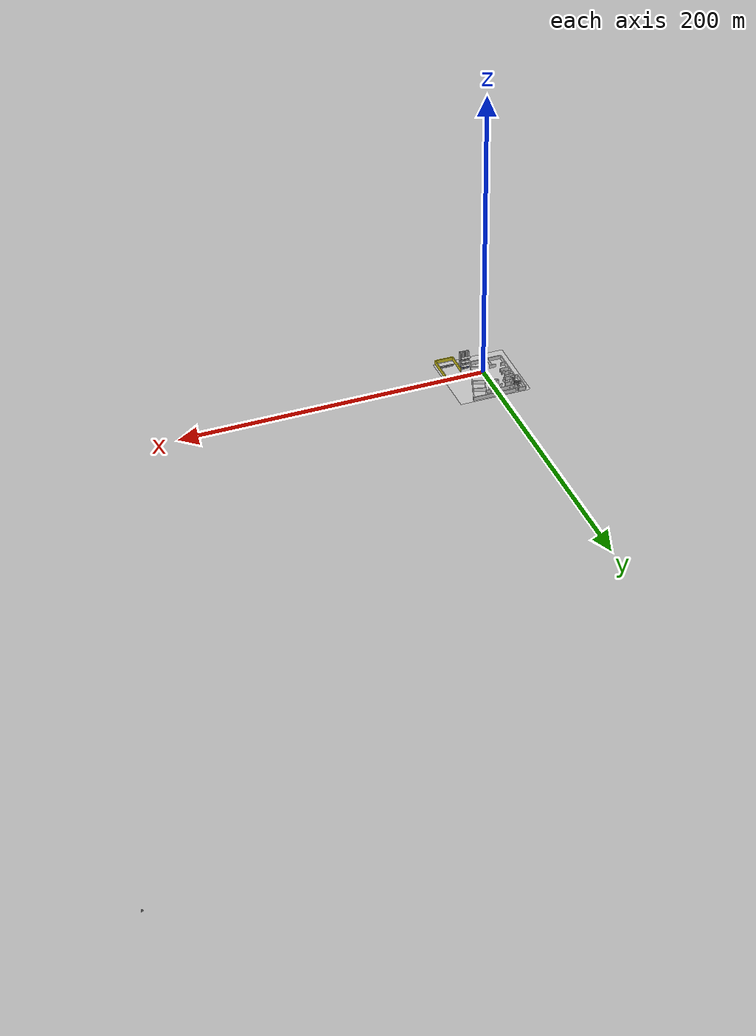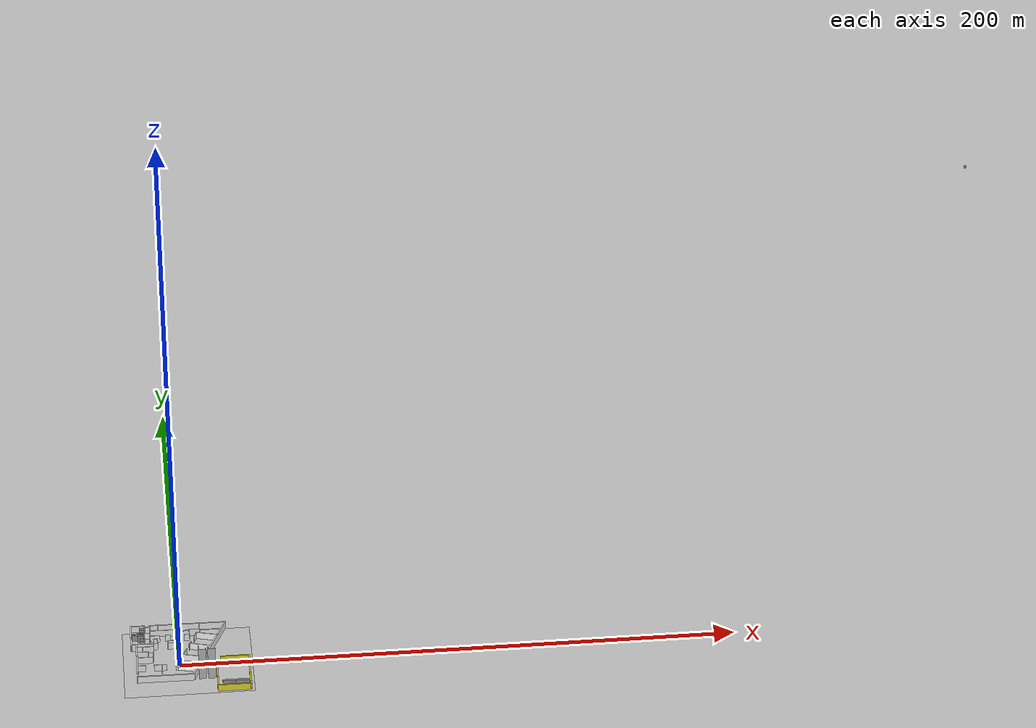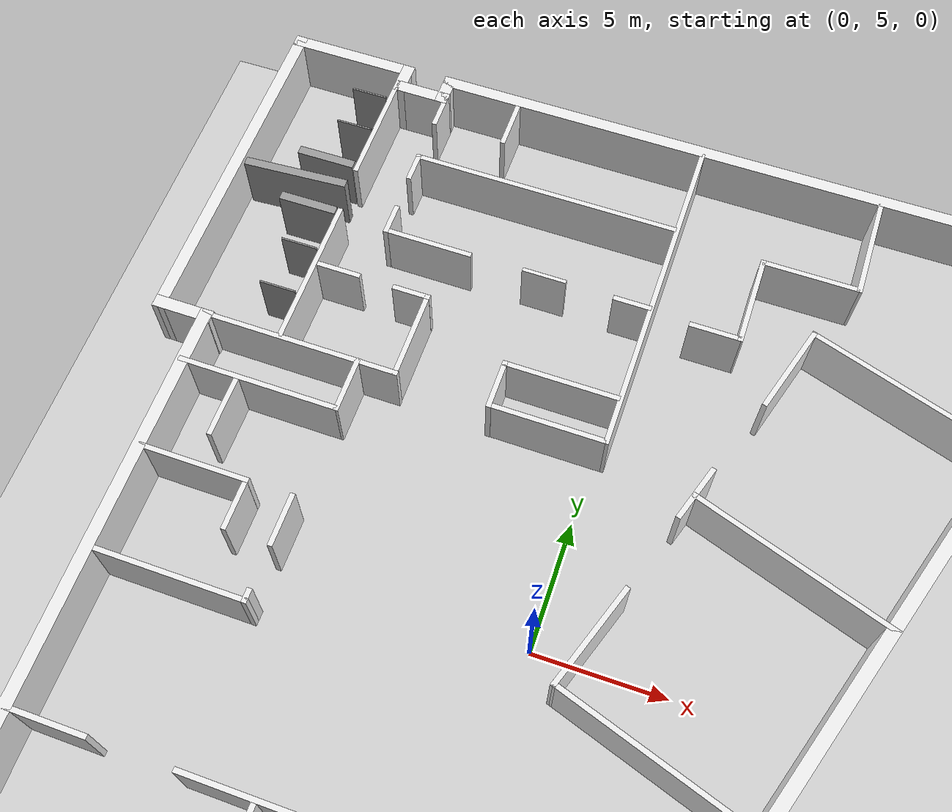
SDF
<sdf version="1.7">
 <world name="default">
  <light name="sun" type="directional">
   <pose>0 0 10 0 -0 0</pose>
   <diffuse>0.8 0.8 0.8 1</diffuse>
   <specular>0.2 0.2 0.2 1</specular>
   <attenuation>
    <range>1000</range>
    <constant>0.9</constant>
    <linear>0.01</linear>
    <quadratic>0.001</quadratic>
   </attenuation>
   <direction>-0.5 0.1 -0.9</direction>
   <spot><inner_angle>0</inner_angle><outer_angle>0</outer_angle><falloff>0</falloff></spot>
  </light>
  <gravity>0 0 -9.8</gravity>
  <magnetic_field>6e-06 2.3e-05 -4.2e-05</magnetic_field>
  <atmosphere type="adiabatic"/>
  <physics type="ode">
   <max_step_size>0.001</max_step_size>
   <real_time_factor>1</real_time_factor>
   <real_time_update_rate>1000</real_time_update_rate>
  </physics>
  <scene><ambient>0.4 0.4 0.4 1</ambient><background>0.7 0.7 0.7 1</background><shadows>1</shadows></scene>
  <spherical_coordinates>
   <surface_model>EARTH_WGS84</surface_model>
   <latitude_deg>0</latitude_deg>
   <longitude_deg>0</longitude_deg>
   <elevation>0</elevation>
   <heading_deg>0</heading_deg>
  </spherical_coordinates>
  <model name="hospital_wall">
   <pose>3.70516 3.23402 0 0 -0 -1.57977</pose>
   <link name="Wall_0">
    <collision name="Wall_0_Collision">
     <geometry><box><size>27.85 0.5 2.5</size></box></geometry>
     <pose>0 0 1.25 0 -0 0</pose>
    </collision>
    <visual name="Wall_0_Visual">
     <pose>0 0 1.25 0 -0 0</pose>
     <geometry><box><size>27.85 0.5 2.5</size></box></geometry>
     <material>
      <script><uri>file://media/materials/scripts/gazebo.material</uri><name>Gazebo/White</name></script>
      <ambient>1 1 1 1</ambient>
     </material>
     <meta><layer>0</layer></meta>
    </visual>
    <pose>-22.6945 -0.556827 0 0 -0 -1.57078</pose>
   </link>
   <link name="Wall_101">
    <collision name="Wall_101_Collision">
     <geometry><box><size>1.25 0.2 2.5</size></box></geometry>
     <pose>0 0 1.25 0 -0 0</pose>
    </collision>
    <visual name="Wall_101_Visual">
     <pose>0 0 1.25 0 -0 0</pose>
     <geometry><box><size>1.25 0.2 2.5</size></box></geometry>
     <material>
      <script><uri>file://media/materials/scripts/gazebo.material</uri><name>Gazebo/White</name></script>
      <ambient>1 1 1 1</ambient>
     </material>
     <meta><layer>0</layer></meta>
    </visual>
    <pose>-18.1899 -14.0971 0 0 -0 3.14159</pose>
   </link>
   <link name="Wall_103">
    <collision name="Wall_103_Collision">
     <geometry><box><size>1.30009 0.2 2.5</size></box></geometry>
     <pose>0 0 1.25 0 -0 0</pose>
    </collision>
    <visual name="Wall_103_Visual">
     <pose>0 0 1.25 0 -0 0</pose>
     <geometry><box><size>1.30009 0.2 2.5</size></box></geometry>
     <material>
      <script><uri>file://media/materials/scripts/gazebo.material</uri><name>Gazebo/White</name></script>
      <ambient>1 1 1 1</ambient>
     </material>
     <meta><layer>0</layer></meta>
    </visual>
    <pose>-15.5522 -14.0461 0 0 -0 0</pose>
   </link>
   <link name="Wall_105">
    <collision name="Wall_105_Collision">
     <geometry><box><size>3.5 0.2 2.5</size></box></geometry>
     <pose>0 0 1.25 0 -0 0</pose>
    </collision>
    <visual name="Wall_105_Visual">
     <pose>0 0 1.25 0 -0 0</pose>
     <geometry><box><size>3.5 0.2 2.5</size></box></geometry>
     <material>
      <script><uri>file://media/materials/scripts/gazebo.material</uri><name>Gazebo/White</name></script>
      <ambient>1 1 1 1</ambient>
     </material>
     <meta><layer>0</layer></meta>
    </visual>
    <pose>-15.0024 -12.3017 0 0 -0 -1.5708</pose>
   </link>
   <link name="Wall_107">
    <collision name="Wall_107_Collision">
     <geometry><box><size>2.25 0.2 2.5</size></box></geometry>
     <pose>0 0 1.25 0 -0 0</pose>
    </collision>
    <visual name="Wall_107_Visual">
     <pose>0 0 1.25 0 -0 0</pose>
     <geometry><box><size>2.25 0.2 2.5</size></box></geometry>
     <material>
      <script><uri>file://media/materials/scripts/gazebo.material</uri><name>Gazebo/White</name></script>
      <ambient>1 1 1 1</ambient>
     </material>
     <meta><layer>0</layer></meta>
    </visual>
    <pose>-21.5791 -11.151 0 0 -0 3.14159</pose>
   </link>
   <link name="Wall_109">
    <collision name="Wall_109_Collision">
     <geometry><box><size>1.5 0.2 2.5</size></box></geometry>
     <pose>0 0 1.25 0 -0 0</pose>
    </collision>
    <visual name="Wall_109_Visual">
     <pose>0 0 1.25 0 -0 0</pose>
     <geometry><box><size>1.5 0.2 2.5</size></box></geometry>
     <material>
      <script><uri>file://media/materials/scripts/gazebo.material</uri><name>Gazebo/White</name></script>
      <ambient>1 1 1 1</ambient>
     </material>
     <meta><layer>0</layer></meta>
    </visual>
    <pose>-12.697 -12.138 0 0 -0 1.5708</pose>
   </link>
   <link name="Wall_111">
    <collision name="Wall_111_Collision">
     <geometry><box><size>6.05 0.2 2.5</size></box></geometry>
     <pose>0 0 1.25 0 -0 0</pose>
    </collision>
    <visual name="Wall_111_Visual">
     <pose>0 0 1.25 0 -0 0</pose>
     <geometry><box><size>6.05 0.2 2.5</size></box></geometry>
     <material>
      <script><uri>file://media/materials/scripts/gazebo.material</uri><name>Gazebo/White</name></script>
      <ambient>1 1 1 1</ambient>
     </material>
     <meta><layer>0</layer></meta>
    </visual>
    <pose>-12.3324 -16.088 0 0 -0 0</pose>
   </link>
   <link name="Wall_113">
    <collision name="Wall_113_Collision">
     <geometry><box><size>1.75 0.2 2.5</size></box></geometry>
     <pose>0 0 1.25 0 -0 0</pose>
    </collision>
    <visual name="Wall_113_Visual">
     <pose>0 0 1.25 0 -0 0</pose>
     <geometry><box><size>1.75 0.2 2.5</size></box></geometry>
     <material>
      <script><uri>file://media/materials/scripts/gazebo.material</uri><name>Gazebo/White</name></script>
      <ambient>1 1 1 1</ambient>
     </material>
     <meta><layer>0</layer></meta>
    </visual>
    <pose>-12.7232 -15.1011 0 0 -0 -1.5708</pose>
   </link>
   <link name="Wall_115">
    <collision name="Wall_115_Collision">
     <geometry><box><size>4.5 0.2 2.5</size></box></geometry>
     <pose>0 0 1.25 0 -0 0</pose>
    </collision>
    <visual name="Wall_115_Visual">
     <pose>0 0 1.25 0 -0 0</pose>
     <geometry><box><size>4.5 0.2 2.5</size></box></geometry>
     <material>
      <script><uri>file://media/materials/scripts/gazebo.material</uri><name>Gazebo/White</name></script>
      <ambient>1 1 1 1</ambient>
     </material>
     <meta><layer>0</layer></meta>
    </visual>
    <pose>-10.9872 -5.67707 0 0 -0 1.5708</pose>
   </link>
   <link name="Wall_117">
    <collision name="Wall_117_Collision">
     <geometry><box><size>4.5 0.2 2.5</size></box></geometry>
     <pose>0 0 1.25 0 -0 0</pose>
    </collision>
    <visual name="Wall_117_Visual">
     <pose>0 0 1.25 0 -0 0</pose>
     <geometry><box><size>4.5 0.2 2.5</size></box></geometry>
     <material>
      <script><uri>file://media/materials/scripts/gazebo.material</uri><name>Gazebo/White</name></script>
      <ambient>1 1 1 1</ambient>
     </material>
     <meta><layer>0</layer></meta>
    </visual>
    <pose>-9.1948 -5.67532 0 0 -0 1.5708</pose>
   </link>
   <link name="Wall_12">
    <collision name="Wall_12_Collision">
     <geometry><box><size>14 0.5 2.5</size></box></geometry>
     <pose>0 0 1.25 0 -0 0</pose>
    </collision>
    <visual name="Wall_12_Visual">
     <pose>0 0 1.25 0 -0 0</pose>
     <geometry><box><size>14 0.5 2.5</size></box></geometry>
     <material>
      <script><uri>file://media/materials/scripts/gazebo.material</uri><name>Gazebo/White</name></script>
      <ambient>1 1 1 1</ambient>
     </material>
     <meta><layer>0</layer></meta>
    </visual>
    <pose>-15.9442 -20.8921 0 0 -0 0</pose>
   </link>
   <link name="Wall_120">
    <collision name="Wall_120_Collision">
     <geometry><box><size>2 0.2 2.5</size></box></geometry>
     <pose>0 0 1.25 0 -0 0</pose>
    </collision>
    <visual name="Wall_120_Visual">
     <pose>0 0 1.25 0 -0 0</pose>
     <geometry><box><size>2 0.2 2.5</size></box></geometry>
     <material>
      <script><uri>file://media/materials/scripts/gazebo.material</uri><name>Gazebo/White</name></script>
      <ambient>1 1 1 1</ambient>
     </material>
     <meta><layer>0</layer></meta>
    </visual>
    <pose>-10.0892 -7.82789 0 0 -0 0</pose>
   </link>
   <link name="Wall_122">
    <collision name="Wall_122_Collision">
     <geometry><box><size>2.5 0.2 2.5</size></box></geometry>
     <pose>0 0 1.25 0 -0 0</pose>
    </collision>
    <visual name="Wall_122_Visual">
     <pose>0 0 1.25 0 -0 0</pose>
     <geometry><box><size>2.5 0.2 2.5</size></box></geometry>
     <material>
      <script><uri>file://media/materials/scripts/gazebo.material</uri><name>Gazebo/White</name></script>
      <ambient>1 1 1 1</ambient>
     </material>
     <meta><layer>0</layer></meta>
    </visual>
    <pose>-6.02163 -16.8589 0 0 -0 3.14159</pose>
   </link>
   <link name="Wall_124">
    <collision name="Wall_124_Collision">
     <geometry><box><size>4.30001 0.2 2.5</size></box></geometry>
     <pose>0 0 1.25 0 -0 0</pose>
    </collision>
    <visual name="Wall_124_Visual">
     <pose>0 0 1.25 0 -0 0</pose>
     <geometry><box><size>4.30001 0.2 2.5</size></box></geometry>
     <material>
      <script><uri>file://media/materials/scripts/gazebo.material</uri><name>Gazebo/White</name></script>
      <ambient>1 1 1 1</ambient>
     </material>
     <meta><layer>0</layer></meta>
    </visual>
    <pose>-3.60823 -16.9331 0 0 -0 -1.5708</pose>
   </link>
   <link name="Wall_126">
    <collision name="Wall_126_Collision">
     <geometry><box><size>2 0.2 2.5</size></box></geometry>
     <pose>0 0 1.25 0 -0 0</pose>
    </collision>
    <visual name="Wall_126_Visual">
     <pose>0 0 1.25 0 -0 0</pose>
     <geometry><box><size>2 0.2 2.5</size></box></geometry>
     <material>
      <script><uri>file://media/materials/scripts/gazebo.material</uri><name>Gazebo/White</name></script>
      <ambient>1 1 1 1</ambient>
     </material>
     <meta><layer>0</layer></meta>
    </visual>
    <pose>-2.64995 -14.8874 0 0 -0 3.14159</pose>
   </link>
   <link name="Wall_128">
    <collision name="Wall_128_Collision">
     <geometry><box><size>0.55 0.2 2.5</size></box></geometry>
     <pose>0 0 1.25 0 -0 0</pose>
    </collision>
    <visual name="Wall_128_Visual">
     <pose>0 0 1.25 0 -0 0</pose>
     <geometry><box><size>0.55 0.2 2.5</size></box></geometry>
     <material>
      <script><uri>file://media/materials/scripts/gazebo.material</uri><name>Gazebo/White</name></script>
      <ambient>1 1 1 1</ambient>
     </material>
     <meta><layer>0</layer></meta>
    </visual>
    <pose>0.233926 -13.1551 0 0 -0 0</pose>
   </link>
   <link name="Wall_130">
    <collision name="Wall_130_Collision">
     <geometry><box><size>6 0.2 2.5</size></box></geometry>
     <pose>0 0 1.25 0 -0 0</pose>
    </collision>
    <visual name="Wall_130_Visual">
     <pose>0 0 1.25 0 -0 0</pose>
     <geometry><box><size>6 0.2 2.5</size></box></geometry>
     <material>
      <script><uri>file://media/materials/scripts/gazebo.material</uri><name>Gazebo/White</name></script>
      <ambient>1 1 1 1</ambient>
     </material>
     <meta><layer>0</layer></meta>
    </visual>
    <pose>0.407767 -16.0541 0 0 -0 1.5708</pose>
   </link>
   <link name="Wall_132">
    <collision name="Wall_132_Collision">
     <geometry><box><size>4.25 0.2 2.5</size></box></geometry>
     <pose>0 0 1.25 0 -0 0</pose>
    </collision>
    <visual name="Wall_132_Visual">
     <pose>0 0 1.25 0 -0 0</pose>
     <geometry><box><size>4.25 0.2 2.5</size></box></geometry>
     <material>
      <script><uri>file://media/materials/scripts/gazebo.material</uri><name>Gazebo/White</name></script>
      <ambient>1 1 1 1</ambient>
     </material>
     <meta><layer>0</layer></meta>
    </visual>
    <pose>-20.4132 3.82393 0 0 -0 0</pose>
   </link>
   <link name="Wall_134">
    <collision name="Wall_134_Collision">
     <geometry><box><size>3.75 0.2 2.5</size></box></geometry>
     <pose>0 0 1.25 0 -0 0</pose>
    </collision>
    <visual name="Wall_134_Visual">
     <pose>0 0 1.25 0 -0 0</pose>
     <geometry><box><size>3.75 0.2 2.5</size></box></geometry>
     <material>
      <script><uri>file://media/materials/scripts/gazebo.material</uri><name>Gazebo/White</name></script>
      <ambient>1 1 1 1</ambient>
     </material>
     <meta><layer>0</layer></meta>
    </visual>
    <pose>-18.387 1.94161 0 0 -0 1.5708</pose>
   </link>
   <link name="Wall_136">
    <collision name="Wall_136_Collision">
     <geometry><box><size>3.75 0.2 2.5</size></box></geometry>
     <pose>0 0 1.25 0 -0 0</pose>
    </collision>
    <visual name="Wall_136_Visual">
     <pose>0 0 1.25 0 -0 0</pose>
     <geometry><box><size>3.75 0.2 2.5</size></box></geometry>
     <material>
      <script><uri>file://media/materials/scripts/gazebo.material</uri><name>Gazebo/White</name></script>
      <ambient>1 1 1 1</ambient>
     </material>
     <meta><layer>0</layer></meta>
    </visual>
    <pose>-16.6135 0.087292 0 0 -0 3.14159</pose>
   </link>
   <link name="Wall_138">
    <collision name="Wall_138_Collision">
     <geometry><box><size>2 0.2 2.5</size></box></geometry>
     <pose>0 0 1.25 0 -0 0</pose>
    </collision>
    <visual name="Wall_138_Visual">
     <pose>0 0 1.25 0 -0 0</pose>
     <geometry><box><size>2 0.2 2.5</size></box></geometry>
     <material>
      <script><uri>file://media/materials/scripts/gazebo.material</uri><name>Gazebo/White</name></script>
      <ambient>1 1 1 1</ambient>
     </material>
     <meta><layer>0</layer></meta>
    </visual>
    <pose>-14.8374 -0.881729 0 0 -0 1.5708</pose>
   </link>
   <link name="Wall_15">
    <collision name="Wall_15_Collision">
     <geometry><box><size>2.3504 0.5 2.5</size></box></geometry>
     <pose>0 0 1.25 0 -0 0</pose>
    </collision>
    <visual name="Wall_15_Visual">
     <pose>0 0 1.25 0 -0 0</pose>
     <geometry><box><size>2.3504 0.5 2.5</size></box></geometry>
     <material>
      <script><uri>file://media/materials/scripts/gazebo.material</uri><name>Gazebo/White</name></script>
      <ambient>1 1 1 1</ambient>
     </material>
     <meta><layer>0</layer></meta>
    </visual>
    <pose>-9.19703 -19.9669 0 0 -0 1.57382</pose>
   </link>
   <link name="Wall_17">
    <collision name="Wall_17_Collision">
     <geometry><box><size>23.6058 0.5 2.5</size></box></geometry>
     <pose>0 0 1.25 0 -0 0</pose>
    </collision>
    <visual name="Wall_17_Visual">
     <pose>0 0 1.25 0 -0 0</pose>
     <geometry><box><size>23.6058 0.5 2.5</size></box></geometry>
     <material>
      <script><uri>file://media/materials/scripts/gazebo.material</uri><name>Gazebo/White</name></script>
      <ambient>1 1 1 1</ambient>
     </material>
     <meta><layer>0</layer></meta>
    </visual>
    <pose>2.35297 -19.0214 0 0 -0 0.004195</pose>
   </link>
   <link name="Wall_19">
    <collision name="Wall_19_Collision">
     <geometry><box><size>20.4027 0.5 2.5</size></box></geometry>
     <pose>0 0 1.25 0 -0 0</pose>
    </collision>
    <visual name="Wall_19_Visual">
     <pose>0 0 1.25 0 -0 0</pose>
     <geometry><box><size>20.4027 0.5 2.5</size></box></geometry>
     <material>
      <script><uri>file://media/materials/scripts/gazebo.material</uri><name>Gazebo/White</name></script>
      <ambient>1 1 1 1</ambient>
     </material>
     <meta><layer>0</layer></meta>
    </visual>
    <pose>13.9058 -8.99341 0 0 -0 1.5708</pose>
   </link>
   <link name="Wall_2">
    <collision name="Wall_2_Collision">
     <geometry><box><size>1.34953 0.5 2.5</size></box></geometry>
     <pose>0 0 1.25 0 -0 0</pose>
    </collision>
    <visual name="Wall_2_Visual">
     <pose>0 0 1.25 0 -0 0</pose>
     <geometry><box><size>1.34953 0.5 2.5</size></box></geometry>
     <material>
      <script><uri>file://media/materials/scripts/gazebo.material</uri><name>Gazebo/White</name></script>
      <ambient>1 1 1 1</ambient>
     </material>
     <meta><layer>0</layer></meta>
    </visual>
    <pose>-22.2692 -14.2321 0 0 -0 0</pose>
   </link>
   <link name="Wall_21">
    <collision name="Wall_21_Collision">
     <geometry><box><size>25.994 0.5 2.5</size></box></geometry>
     <pose>0 0 1.25 0 -0 0</pose>
    </collision>
    <visual name="Wall_21_Visual">
     <pose>0 0 1.25 0 -0 0</pose>
     <geometry><box><size>25.994 0.5 2.5</size></box></geometry>
     <material>
      <script><uri>file://media/materials/scripts/gazebo.material</uri><name>Gazebo/White</name></script>
      <ambient>1 1 1 1</ambient>
     </material>
     <meta><layer>0</layer></meta>
    </visual>
    <pose>-10.1882 9.03243 0 0 -0 -0.321217</pose>
   </link>
   <link name="Wall_23">
    <collision name="Wall_23_Collision">
     <geometry><box><size>5.92015 0.5 2.5</size></box></geometry>
     <pose>0 0 1.25 0 -0 0</pose>
    </collision>
    <visual name="Wall_23_Visual">
     <pose>0 0 1.25 0 -0 0</pose>
     <geometry><box><size>5.92015 0.5 2.5</size></box></geometry>
     <material>
      <script><uri>file://media/materials/scripts/gazebo.material</uri><name>Gazebo/White</name></script>
      <ambient>1 1 1 1</ambient>
     </material>
     <meta><layer>0</layer></meta>
    </visual>
    <pose>11.2768 1.89793 0 0 -0 -0.322917</pose>
   </link>
   <link name="Wall_25">
    <collision name="Wall_25_Collision">
     <geometry><box><size>10.25 0.5 2.5</size></box></geometry>
     <pose>0 0 1.25 0 -0 0</pose>
    </collision>
    <visual name="Wall_25_Visual">
     <pose>0 0 1.25 0 -0 0</pose>
     <geometry><box><size>10.25 0.5 2.5</size></box></geometry>
     <material>
      <script><uri>file://media/materials/scripts/gazebo.material</uri><name>Gazebo/Yellow</name></script>
      <ambient>1 1 1 1</ambient>
     </material>
     <meta><layer>0</layer></meta>
    </visual>
    <pose>2.44213 15.8139 0 0 -0 1.5708</pose>
   </link>
   <link name="Wall_29">
    <collision name="Wall_29_Collision">
     <geometry><box><size>14 0.5 2.5</size></box></geometry>
     <pose>0 0 1.25 0 -0 0</pose>
    </collision>
    <visual name="Wall_29_Visual">
     <pose>0 0 1.25 0 -0 0</pose>
     <geometry><box><size>14 0.5 2.5</size></box></geometry>
     <material>
      <script><uri>file://media/materials/scripts/gazebo.material</uri><name>Gazebo/Yellow</name></script>
      <ambient>1 1 1 1</ambient>
     </material>
     <meta><layer>0</layer></meta>
    </visual>
    <pose>15.9259 9.2975 0 0 -0 0</pose>
   </link>
   <link name="Wall_31">
    <collision name="Wall_31_Collision">
     <geometry><box><size>11.6 0.5 2.5</size></box></geometry>
     <pose>0 0 1.25 0 -0 0</pose>
    </collision>
    <visual name="Wall_31_Visual">
     <pose>0 0 1.25 0 -0 0</pose>
     <geometry><box><size>11.6 0.5 2.5</size></box></geometry>
     <material>
      <script><uri>file://media/materials/scripts/gazebo.material</uri><name>Gazebo/Yellow</name></script>
      <ambient>1 1 1 1</ambient>
     </material>
     <meta><layer>0</layer></meta>
    </visual>
    <pose>22.6947 14.9589 0 0 -0 1.5708</pose>
   </link>
   <link name="Wall_33">
    <collision name="Wall_33_Collision">
     <geometry><box><size>20.75 0.5 2.5</size></box></geometry>
     <pose>0 0 1.25 0 -0 0</pose>
    </collision>
    <visual name="Wall_33_Visual">
     <pose>0 0 1.25 0 -0 0</pose>
     <geometry><box><size>20.75 0.5 2.5</size></box></geometry>
     <material>
      <script><uri>file://media/materials/scripts/gazebo.material</uri><name>Gazebo/Yellow</name></script>
      <ambient>1 1 1 1</ambient>
     </material>
     <meta><layer>0</layer></meta>
    </visual>
    <pose>12.5443 20.8928 0 0 -0 3.14159</pose>
   </link>
   <link name="Wall_36">
    <collision name="Wall_36_Collision">
     <geometry><box><size>8.02379 0.2 2.5</size></box></geometry>
     <pose>0 0 1.25 0 -0 0</pose>
    </collision>
    <visual name="Wall_36_Visual">
     <pose>0 0 1.25 0 -0 0</pose>
     <geometry><box><size>8.02379 0.2 2.5</size></box></geometry>
     <material>
      <script><uri>file://media/materials/scripts/gazebo.material</uri><name>Gazebo/White</name></script>
      <ambient>1 1 1 1</ambient>
     </material>
     <meta><layer>0</layer></meta>
    </visual>
    <pose>0.840579 1.20633 0 0 -0 1.26174</pose>
   </link>
   <link name="Wall_38">
    <collision name="Wall_38_Collision">
     <geometry><box><size>7.84014 0.2 2.5</size></box></geometry>
     <pose>0 0 1.25 0 -0 0</pose>
    </collision>
    <visual name="Wall_38_Visual">
     <pose>0 0 1.25 0 -0 0</pose>
     <geometry><box><size>7.84014 0.2 2.5</size></box></geometry>
     <material>
      <script><uri>file://media/materials/scripts/gazebo.material</uri><name>Gazebo/White</name></script>
      <ambient>1 1 1 1</ambient>
     </material>
     <meta><layer>0</layer></meta>
    </visual>
    <pose>7.39677 -0.912771 0 0 -0 1.26775</pose>
   </link>
   <link name="Wall_40">
    <collision name="Wall_40_Collision">
     <geometry><box><size>0.75 0.2 2.5</size></box></geometry>
     <pose>0 0 1.25 0 -0 0</pose>
    </collision>
    <visual name="Wall_40_Visual">
     <pose>0 0 1.25 0 -0 0</pose>
     <geometry><box><size>0.75 0.2 2.5</size></box></geometry>
     <material>
      <script><uri>file://media/materials/scripts/gazebo.material</uri><name>Gazebo/White</name></script>
      <ambient>1 1 1 1</ambient>
     </material>
     <meta><layer>0</layer></meta>
    </visual>
    <pose>6.25677 -4.94668 0 0 -0 1.5708</pose>
   </link>
   <link name="Wall_42">
    <collision name="Wall_42_Collision">
     <geometry><box><size>4.54982 0.2 2.5</size></box></geometry>
     <pose>0 0 1.25 0 -0 0</pose>
    </collision>
    <visual name="Wall_42_Visual">
     <pose>0 0 1.25 0 -0 0</pose>
     <geometry><box><size>4.54982 0.2 2.5</size></box></geometry>
     <material>
      <script><uri>file://media/materials/scripts/gazebo.material</uri><name>Gazebo/White</name></script>
      <ambient>1 1 1 1</ambient>
     </material>
     <meta><layer>0</layer></meta>
    </visual>
    <pose>6.18977 -10.7381 0 0 -0 -1.5708</pose>
   </link>
   <link name="Wall_45">
    <collision name="Wall_45_Collision">
     <geometry><box><size>3.05045 0.2 2.5</size></box></geometry>
     <pose>0 0 1.25 0 -0 0</pose>
    </collision>
    <visual name="Wall_45_Visual">
     <pose>0 0 1.25 0 -0 0</pose>
     <geometry><box><size>3.05045 0.2 2.5</size></box></geometry>
     <material>
      <script><uri>file://media/materials/scripts/gazebo.material</uri><name>Gazebo/White</name></script>
      <ambient>1 1 1 1</ambient>
     </material>
     <meta><layer>0</layer></meta>
    </visual>
    <pose>6.19877 -17.5651 0 0 -0 -1.5708</pose>
   </link>
   <link name="Wall_47">
    <collision name="Wall_47_Collision">
     <geometry><box><size>7.79995 0.2 2.5</size></box></geometry>
     <pose>0 0 1.25 0 -0 0</pose>
    </collision>
    <visual name="Wall_47_Visual">
     <pose>0 0 1.25 0 -0 0</pose>
     <geometry><box><size>7.79995 0.2 2.5</size></box></geometry>
     <material>
      <script><uri>file://media/materials/scripts/gazebo.material</uri><name>Gazebo/White</name></script>
      <ambient>1 1 1 1</ambient>
     </material>
     <meta><layer>0</layer></meta>
    </visual>
    <pose>10.1328 -10.2061 0 0 -0 0</pose>
   </link>
   <link name="Wall_5">
    <collision name="Wall_5_Collision">
     <geometry><box><size>2.35 0.5 2.5</size></box></geometry>
     <pose>0 0 1.25 0 -0 0</pose>
    </collision>
    <visual name="Wall_5_Visual">
     <pose>0 0 1.25 0 -0 0</pose>
     <geometry><box><size>2.35 0.5 2.5</size></box></geometry>
     <material>
      <script><uri>file://media/materials/scripts/gazebo.material</uri><name>Gazebo/White</name></script>
      <ambient>1 1 1 1</ambient>
     </material>
     <meta><layer>0</layer></meta>
    </visual>
    <pose>-21.8442 -15.1571 0 0 -0 -1.5708</pose>
   </link>
   <link name="Wall_58">
    <collision name="Wall_58_Collision">
     <geometry><box><size>4.27097 0.2 2.5</size></box></geometry>
     <pose>0 0 1.25 0 -0 0</pose>
    </collision>
    <visual name="Wall_58_Visual">
     <pose>0 0 1.25 0 -0 0</pose>
     <geometry><box><size>4.27097 0.2 2.5</size></box></geometry>
     <material>
      <script><uri>file://media/materials/scripts/gazebo.material</uri><name>Gazebo/White</name></script>
      <ambient>1 1 1 1</ambient>
     </material>
     <meta><layer>0</layer></meta>
    </visual>
    <pose>-2.27423 -1.85857 0 0 -0 -0.330994</pose>
   </link>
   <link name="Wall_60">
    <collision name="Wall_60_Collision">
     <geometry><box><size>2.33146 0.2 2.5</size></box></geometry>
     <pose>0 0 1.25 0 -0 0</pose>
    </collision>
    <visual name="Wall_60_Visual">
     <pose>0 0 1.25 0 -0 0</pose>
     <geometry><box><size>2.33146 0.2 2.5</size></box></geometry>
     <material>
      <script><uri>file://media/materials/scripts/gazebo.material</uri><name>Gazebo/White</name></script>
      <ambient>1 1 1 1</ambient>
     </material>
     <meta><layer>0</layer></meta>
    </visual>
    <pose>-8.34323 0.115928 0 0 -0 -0.312849</pose>
   </link>
   <link name="Wall_65">
    <collision name="Wall_65_Collision">
     <geometry><box><size>8.18103 0.2 2.5</size></box></geometry>
     <pose>0 0 1.25 0 -0 0</pose>
    </collision>
    <visual name="Wall_65_Visual">
     <pose>0 0 1.25 0 -0 0</pose>
     <geometry><box><size>8.18103 0.2 2.5</size></box></geometry>
     <material>
      <script><uri>file://media/materials/scripts/gazebo.material</uri><name>Gazebo/White</name></script>
      <ambient>1 1 1 1</ambient>
     </material>
     <meta><layer>0</layer></meta>
    </visual>
    <pose>-6.99923 3.88693 0 0 -0 1.25325</pose>
   </link>
   <link name="Wall_68">
    <collision name="Wall_68_Collision">
     <geometry><box><size>8.11404 0.2 2.5</size></box></geometry>
     <pose>0 0 1.25 0 -0 0</pose>
    </collision>
    <visual name="Wall_68_Visual">
     <pose>0 0 1.25 0 -0 0</pose>
     <geometry><box><size>8.11404 0.2 2.5</size></box></geometry>
     <material>
      <script><uri>file://media/materials/scripts/gazebo.material</uri><name>Gazebo/White</name></script>
      <ambient>1 1 1 1</ambient>
     </material>
     <meta><layer>0</layer></meta>
    </visual>
    <pose>-14.7317 6.38193 0 0 -0 1.25964</pose>
   </link>
   <link name="Wall_7">
    <collision name="Wall_7_Collision">
     <geometry><box><size>1.35 0.5 2.5</size></box></geometry>
     <pose>0 0 1.25 0 -0 0</pose>
    </collision>
    <visual name="Wall_7_Visual">
     <pose>0 0 1.25 0 -0 0</pose>
     <geometry><box><size>1.35 0.5 2.5</size></box></geometry>
     <material>
      <script><uri>file://media/materials/scripts/gazebo.material</uri><name>Gazebo/White</name></script>
      <ambient>1 1 1 1</ambient>
     </material>
     <meta><layer>0</layer></meta>
    </visual>
    <pose>-22.2692 -16.0821 0 0 -0 3.14159</pose>
   </link>
   <link name="Wall_70">
    <collision name="Wall_70_Collision">
     <geometry><box><size>3.72528 0.2 2.5</size></box></geometry>
     <pose>0 0 1.25 0 -0 0</pose>
    </collision>
    <visual name="Wall_70_Visual">
     <pose>0 0 1.25 0 -0 0</pose>
     <geometry><box><size>3.72528 0.2 2.5</size></box></geometry>
     <material>
      <script><uri>file://media/materials/scripts/gazebo.material</uri><name>Gazebo/White</name></script>
      <ambient>1 1 1 1</ambient>
     </material>
     <meta><layer>0</layer></meta>
    </visual>
    <pose>-14.2362 2.09543 0 0 -0 -0.292055</pose>
   </link>
   <link name="Wall_72">
    <collision name="Wall_72_Collision">
     <geometry><box><size>6.25 0.2 2.5</size></box></geometry>
     <pose>0 0 1.25 0 -0 0</pose>
    </collision>
    <visual name="Wall_72_Visual">
     <pose>0 0 1.25 0 -0 0</pose>
     <geometry><box><size>6.25 0.2 2.5</size></box></geometry>
     <material>
      <script><uri>file://media/materials/scripts/gazebo.material</uri><name>Gazebo/White</name></script>
      <ambient>1 1 1 1</ambient>
     </material>
     <meta><layer>0</layer></meta>
    </visual>
    <pose>-7.24323 -16.0931 0 0 -0 -1.5708</pose>
   </link>
   <link name="Wall_77">
    <collision name="Wall_77_Collision">
     <geometry><box><size>6.25 0.2 2.5</size></box></geometry>
     <pose>0 0 1.25 0 -0 0</pose>
    </collision>
    <visual name="Wall_77_Visual">
     <pose>0 0 1.25 0 -0 0</pose>
     <geometry><box><size>6.25 0.2 2.5</size></box></geometry>
     <material>
      <script><uri>file://media/materials/scripts/gazebo.material</uri><name>Gazebo/White</name></script>
      <ambient>1 1 1 1</ambient>
     </material>
     <meta><layer>0</layer></meta>
    </visual>
    <pose>-9.29023 -16.0101 0 0 -0 1.5708</pose>
   </link>
   <link name="Wall_81">
    <collision name="Wall_81_Collision">
     <geometry><box><size>2.25 0.2 2.5</size></box></geometry>
     <pose>0 0 1.25 0 -0 0</pose>
    </collision>
    <visual name="Wall_81_Visual">
     <pose>0 0 1.25 0 -0 0</pose>
     <geometry><box><size>2.25 0.2 2.5</size></box></geometry>
     <material>
      <script><uri>file://media/materials/scripts/gazebo.material</uri><name>Gazebo/White</name></script>
      <ambient>1 1 1 1</ambient>
     </material>
     <meta><layer>0</layer></meta>
    </visual>
    <pose>-8.2697 -12.9678 0 0 -0 0</pose>
   </link>
   <link name="Wall_83">
    <collision name="Wall_83_Collision">
     <geometry><box><size>2.04976 0.2 2.5</size></box></geometry>
     <pose>0 0 1.25 0 -0 0</pose>
    </collision>
    <visual name="Wall_83_Visual">
     <pose>0 0 1.25 0 -0 0</pose>
     <geometry><box><size>2.04976 0.2 2.5</size></box></geometry>
     <material>
      <script><uri>file://media/materials/scripts/gazebo.material</uri><name>Gazebo/White</name></script>
      <ambient>1 1 1 1</ambient>
     </material>
     <meta><layer>0</layer></meta>
    </visual>
    <pose>-2.65423 -13.1321 0 0 -0 0</pose>
   </link>
   <link name="Wall_85">
    <collision name="Wall_85_Collision">
     <geometry><box><size>1.55 0.2 2.5</size></box></geometry>
     <pose>0 0 1.25 0 -0 0</pose>
    </collision>
    <visual name="Wall_85_Visual">
     <pose>0 0 1.25 0 -0 0</pose>
     <geometry><box><size>1.55 0.2 2.5</size></box></geometry>
     <material>
      <script><uri>file://media/materials/scripts/gazebo.material</uri><name>Gazebo/White</name></script>
      <ambient>1 1 1 1</ambient>
     </material>
     <meta><layer>0</layer></meta>
    </visual>
    <pose>-9.28482 -12.1541 0 0 -0 -1.5708</pose>
   </link>
   <link name="Wall_87">
    <collision name="Wall_87_Collision">
     <geometry><box><size>3.5 0.2 2.5</size></box></geometry>
     <pose>0 0 1.25 0 -0 0</pose>
    </collision>
    <visual name="Wall_87_Visual">
     <pose>0 0 1.25 0 -0 0</pose>
     <geometry><box><size>3.5 0.2 2.5</size></box></geometry>
     <material>
      <script><uri>file://media/materials/scripts/gazebo.material</uri><name>Gazebo/White</name></script>
      <ambient>1 1 1 1</ambient>
     </material>
     <meta><layer>0</layer></meta>
    </visual>
    <pose>-10.9541 -11.492 0 0 -0 0</pose>
   </link>
   <link name="Wall_89">
    <collision name="Wall_89_Collision">
     <geometry><box><size>4.5 0.2 2.5</size></box></geometry>
     <pose>0 0 1.25 0 -0 0</pose>
    </collision>
    <visual name="Wall_89_Visual">
     <pose>0 0 1.25 0 -0 0</pose>
     <geometry><box><size>4.5 0.2 2.5</size></box></geometry>
     <material>
      <script><uri>file://media/materials/scripts/gazebo.material</uri><name>Gazebo/White</name></script>
      <ambient>1 1 1 1</ambient>
     </material>
     <meta><layer>0</layer></meta>
    </visual>
    <pose>-19.4706 -16.2291 0 0 -0 0</pose>
   </link>
   <link name="Wall_9">
    <collision name="Wall_9_Collision">
     <geometry><box><size>5.31023 0.5 2.5</size></box></geometry>
     <pose>0 0 1.25 0 -0 0</pose>
    </collision>
    <visual name="Wall_9_Visual">
     <pose>0 0 1.25 0 -0 0</pose>
     <geometry><box><size>5.31023 0.5 2.5</size></box></geometry>
     <material>
      <script><uri>file://media/materials/scripts/gazebo.material</uri><name>Gazebo/White</name></script>
      <ambient>1 1 1 1</ambient>
     </material>
     <meta><layer>0</layer></meta>
    </visual>
    <pose>-22.6942 -18.4871 0 0 -0 -1.5708</pose>
   </link>
   <link name="Wall_91">
    <collision name="Wall_91_Collision">
     <geometry><box><size>13.5 0.2 2.5</size></box></geometry>
     <pose>0 0 1.25 0 -0 0</pose>
    </collision>
    <visual name="Wall_91_Visual">
     <pose>0 0 1.25 0 -0 0</pose>
     <geometry><box><size>13.5 0.2 2.5</size></box></geometry>
     <material>
      <script><uri>file://media/materials/scripts/gazebo.material</uri><name>Gazebo/White</name></script>
      <ambient>1 1 1 1</ambient>
     </material>
     <meta><layer>0</layer></meta>
    </visual>
    <pose>-15.8452 -3.39907 0 0 -0 0</pose>
   </link>
   <link name="Wall_93">
    <collision name="Wall_93_Collision">
     <geometry><box><size>1.5 0.2 2.5</size></box></geometry>
     <pose>0 0 1.25 0 -0 0</pose>
    </collision>
    <visual name="Wall_93_Visual">
     <pose>0 0 1.25 0 -0 0</pose>
     <geometry><box><size>1.5 0.2 2.5</size></box></geometry>
     <material>
      <script><uri>file://media/materials/scripts/gazebo.material</uri><name>Gazebo/White</name></script>
      <ambient>1 1 1 1</ambient>
     </material>
     <meta><layer>0</layer></meta>
    </visual>
    <pose>-14.9992 -4.12907 0 0 -0 1.5708</pose>
   </link>
   <link name="Wall_95">
    <collision name="Wall_95_Collision">
     <geometry><box><size>1.75 0.15 2.5</size></box></geometry>
     <pose>0 0 1.25 0 -0 0</pose>
    </collision>
    <visual name="Wall_95_Visual">
     <pose>0 0 1.25 0 -0 0</pose>
     <geometry><box><size>1.75 0.15 2.5</size></box></geometry>
     <material>
      <script><uri>file://media/materials/scripts/gazebo.material</uri><name>Gazebo/White</name></script>
      <ambient>1 1 1 1</ambient>
     </material>
     <meta><layer>0</layer></meta>
    </visual>
    <pose>-15.0568 -7.62987 0 0 -0 -1.5708</pose>
   </link>
   <link name="Wall_97">
    <collision name="Wall_97_Collision">
     <geometry><box><size>10.75 0.2 2.5</size></box></geometry>
     <pose>0 0 1.25 0 -0 0</pose>
    </collision>
    <visual name="Wall_97_Visual">
     <pose>0 0 1.25 0 -0 0</pose>
     <geometry><box><size>10.75 0.2 2.5</size></box></geometry>
     <material>
      <script><uri>file://media/materials/scripts/gazebo.material</uri><name>Gazebo/White</name></script>
      <ambient>1 1 1 1</ambient>
     </material>
     <meta><layer>0</layer></meta>
    </visual>
    <pose>-18.7202 -8.82507 0 0 -0 -1.5708</pose>
   </link>
   <link name="Wall_99">
    <collision name="Wall_99_Collision">
     <geometry><box><size>1.5 0.2 2.5</size></box></geometry>
     <pose>0 0 1.25 0 -0 0</pose>
    </collision>
    <visual name="Wall_99_Visual">
     <pose>0 0 1.25 0 -0 0</pose>
     <geometry><box><size>1.5 0.2 2.5</size></box></geometry>
     <material>
      <script><uri>file://media/materials/scripts/gazebo.material</uri><name>Gazebo/White</name></script>
      <ambient>1 1 1 1</ambient>
     </material>
     <meta><layer>0</layer></meta>
    </visual>
    <pose>-21.1918 -14.0784 0 0 -0 3.14159</pose>
   </link>
   <static>1</static>
  </model>
  <model name="my_ground_plane">
   <static>1</static>
   <link name="link">
    <collision name="collision">
     <geometry><plane><normal>0 0 1</normal><size>6 6</size></plane></geometry>
     <surface><friction><ode><mu2>1</mu2><mu1>1</mu1></ode></friction></surface>
    </collision>
    <visual name="visual">
     <geometry><plane><normal>0 0 1</normal><size>46 46</size></plane></geometry>
     <cast_shadows>0</cast_shadows>
     <material>
      <script>
       <uri>model://my_ground_plane/materials/scripts</uri>
       <uri>model://my_ground_plane/materials/textures</uri>
       <name>MyGroundPlane/Texture1</name>
      </script>
     </material>
    </visual>
   </link>
   <pose>2.78178 3.19727 0 0 -0 0</pose>
  </model>
  <light name="user_spot_light_0" type="spot">
   <pose>-4.40551 4.60967 1 0 -0 0</pose>
   <diffuse>0.5 0.5 0.5 1</diffuse>
   <specular>0.1 0.1 0.1 1</specular>
   <direction>0 0 -1</direction>
   <attenuation>
    <range>20</range>
    <constant>0.5</constant>
    <linear>0.01</linear>
    <quadratic>0.001</quadratic>
   </attenuation>
   <cast_shadows>0</cast_shadows>
   <spot><inner_angle>0.6</inner_angle><outer_angle>1</outer_angle><falloff>1</falloff></spot>
  </light>
  <model name="beer">
   <link name="link">
    <pose>0 0 0.115 0 -0 0</pose>
    <inertial>
     <mass>0.39</mass>
     <inertia><ixx>0.00058</ixx><ixy>0</ixy><ixz>0</ixz><iyy>0.00058</iyy><iyz>0</iyz><izz>0.00019</izz></inertia>
    </inertial>
    <collision name="collision">
     <geometry><cylinder><radius>0.055</radius><length>0.23</length></cylinder></geometry>
    </collision>
    <visual name="visual">
     <geometry><cylinder><radius>0.055</radius><length>0.23</length></cylinder></geometry>
     <material>
      <script>
       <uri>model://beer/materials/scripts</uri>
       <uri>model://beer/materials/textures</uri>
       <name>Beer/Diffuse</name>
      </script>
     </material>
    </visual>
   </link>
   <pose>2.13181 -8.25349 1.19999 -2.5e-05 -4.4e-05 -0.000746</pose>
  </model>
  <model name="unit_box_clone_clone_0_clone">
   <pose>-13.2323 22.7198 1.26094 1e-05 -1e-06 0.000751</pose>
   <link name="link">
    <inertial>
     <mass>1</mass>
     <inertia>
      <ixx>0.166667</ixx>
      <ixy>0</ixy>
      <ixz>0</ixz>
      <iyy>0.166667</iyy>
      <iyz>0</iyz>
      <izz>0.166667</izz>
     </inertia>
    </inertial>
    <collision name="collision"><geometry><box><size>1.45302 0.065809 2.52188</size></box></geometry></collision>
    <visual name="visual">
     <geometry><box><size>1.45302 0.065809 2.52188</size></box></geometry>
     <material>
      <script><name>Gazebo/Grey</name><uri>file://media/materials/scripts/gazebo.material</uri></script>
     </material>
    </visual>
   </link>
  </model>
  <model name="unit_box_clone_clone_0_clone_clone_1">
   <pose>-13.2378 24.4436 1.26094 1.1e-05 -3e-06 0.000809</pose>
   <link name="link">
    <inertial>
     <mass>1</mass>
     <inertia>
      <ixx>0.166667</ixx>
      <ixy>0</ixy>
      <ixz>0</ixz>
      <iyy>0.166667</iyy>
      <iyz>0</iyz>
      <izz>0.166667</izz>
     </inertia>
    </inertial>
    <collision name="collision"><geometry><box><size>1.45302 0.065809 2.52188</size></box></geometry></collision>
    <visual name="visual">
     <geometry><box><size>1.45302 0.065809 2.52188</size></box></geometry>
     <material>
      <script><name>Gazebo/Grey</name><uri>file://media/materials/scripts/gazebo.material</uri></script>
     </material>
    </visual>
   </link>
  </model>
  <model name="unit_box_clone_clone_0_clone_clone_2">
   <pose>-13.694 20.8525 1.26094 1e-06 -0 0.000747</pose>
   <link name="link">
    <inertial>
     <mass>1</mass>
     <inertia>
      <ixx>0.166667</ixx>
      <ixy>0</ixy>
      <ixz>0</ixz>
      <iyy>0.166667</iyy>
      <iyz>0</iyz>
      <izz>0.166667</izz>
     </inertia>
    </inertial>
    <collision name="collision"><geometry><box><size>2.32458 0.352126 2.52188</size></box></geometry></collision>
    <visual name="visual">
     <geometry><box><size>2.32458 0.352126 2.52188</size></box></geometry>
     <material>
      <script><name>Gazebo/Grey</name><uri>file://media/materials/scripts/gazebo.material</uri></script>
     </material>
    </visual>
   </link>
  </model>
  <model name="unit_box_clone_clone_0_clone_clone_2_clone">
   <pose>-13.545 18.5635 1.26094 1e-06 0 0.000672</pose>
   <link name="link">
    <inertial>
     <mass>1</mass>
     <inertia>
      <ixx>0.166667</ixx>
      <ixy>0</ixy>
      <ixz>0</ixz>
      <iyy>0.166667</iyy>
      <iyz>0</iyz>
      <izz>0.166667</izz>
     </inertia>
    </inertial>
    <collision name="collision"><geometry><box><size>2.32458 0.352126 2.52188</size></box></geometry></collision>
    <visual name="visual">
     <geometry><box><size>2.32458 0.352126 2.52188</size></box></geometry>
     <material>
      <script><name>Gazebo/Grey</name><uri>file://media/materials/scripts/gazebo.material</uri></script>
     </material>
    </visual>
   </link>
  </model>
  <model name="unit_box_clone_clone_0_clone_clone">
   <pose>-13.1613 16.6981 1.26094 0 1e-06 4e-06</pose>
   <link name="link">
    <inertial>
     <mass>1</mass>
     <inertia>
      <ixx>0.166667</ixx>
      <ixy>0</ixy>
      <ixz>0</ixz>
      <iyy>0.166667</iyy>
      <iyz>0</iyz>
      <izz>0.166667</izz>
     </inertia>
    </inertial>
    <collision name="collision"><geometry><box><size>1.45302 0.065809 2.52188</size></box></geometry></collision>
    <visual name="visual">
     <geometry><box><size>1.45302 0.065809 2.52188</size></box></geometry>
     <material>
      <script><name>Gazebo/Grey</name><uri>file://media/materials/scripts/gazebo.material</uri></script>
     </material>
    </visual>
   </link>
  </model>
  <model name="unit_box_clone_clone_0_clone_clone_0">
   <pose>-13.1945 14.6389 1.26094 3e-06 -3e-06 -3e-06</pose>
   <link name="link">
    <inertial>
     <mass>1</mass>
     <inertia>
      <ixx>0.166667</ixx>
      <ixy>0</ixy>
      <ixz>0</ixz>
      <iyy>0.166667</iyy>
      <iyz>0</iyz>
      <izz>0.166667</izz>
     </inertia>
    </inertial>
    <collision name="collision"><geometry><box><size>1.45302 0.065809 2.52188</size></box></geometry></collision>
    <visual name="visual">
     <geometry><box><size>1.45302 0.065809 2.52188</size></box></geometry>
     <material>
      <script><name>Gazebo/Grey</name><uri>file://media/materials/scripts/gazebo.material</uri></script>
     </material>
    </visual>
   </link>
  </model>
  <model name="unit_box_clone_clone_0_clone_clone_2_clone_0">
   <pose>-14.5817 19.7704 1.26069 7e-06 0.000118 0.056258</pose>
   <link name="link">
    <inertial>
     <mass>1</mass>
     <inertia>
      <ixx>0.166667</ixx>
      <ixy>0</ixy>
      <ixz>0</ixz>
      <iyy>0.166667</iyy>
      <iyz>0</iyz>
      <izz>0.166667</izz>
     </inertia>
    </inertial>
    <collision name="collision"><geometry><box><size>4.20858 0.352126 2.52188</size></box></geometry></collision>
    <visual name="visual">
     <geometry><box><size>4.20858 0.352126 2.52188</size></box></geometry>
     <material>
      <script><name>Gazebo/Grey</name><uri>file://media/materials/scripts/gazebo.material</uri></script>
     </material>
    </visual>
   </link>
  </model>
  <light name="user_spot_light_1" type="spot">
   <pose>1.76268 -8.17066 1 0 -0 0</pose>
   <diffuse>0.5 0.5 0.5 1</diffuse>
   <specular>0.1 0.1 0.1 1</specular>
   <direction>0 0 -1</direction>
   <attenuation>
    <range>20</range>
    <constant>0.5</constant>
    <linear>0.01</linear>
    <quadratic>0.001</quadratic>
   </attenuation>
   <cast_shadows>0</cast_shadows>
   <spot><inner_angle>0.6</inner_angle><outer_angle>1</outer_angle><falloff>1</falloff></spot>
  </light>
  <light name="user_spot_light_1_clone" type="spot">
   <pose>0.482746 -6.16552 2.2603 0 -0 0</pose>
   <diffuse>0.5 0.5 0.5 1</diffuse>
   <specular>0.1 0.1 0.1 1</specular>
   <direction>0 0 -1</direction>
   <attenuation>
    <range>20</range>
    <constant>0.5</constant>
    <linear>0.01</linear>
    <quadratic>0.001</quadratic>
   </attenuation>
   <cast_shadows>0</cast_shadows>
   <spot><inner_angle>0.6</inner_angle><outer_angle>1</outer_angle><falloff>1</falloff></spot>
  </light>
  <light name="user_spot_light_1_clone_1" type="spot">
   <pose>-3.80627 -6.14709 2.2603 0 -0 0</pose>
   <diffuse>0.5 0.5 0.5 1</diffuse>
   <specular>0.1 0.1 0.1 1</specular>
   <direction>0 0 -1</direction>
   <attenuation>
    <range>20</range>
    <constant>0.5</constant>
    <linear>0.01</linear>
    <quadratic>0.001</quadratic>
   </attenuation>
   <cast_shadows>0</cast_shadows>
   <spot><inner_angle>0.6</inner_angle><outer_angle>1</outer_angle><falloff>1</falloff></spot>
  </light>
  <light name="user_spot_light_1_clone_0" type="spot">
   <pose>-2.11123 -8.14853 2.2603 0 -0 0</pose>
   <diffuse>0.5 0.5 0.5 1</diffuse>
   <specular>0.1 0.1 0.1 1</specular>
   <direction>0 0 -1</direction>
   <attenuation>
    <range>20</range>
    <constant>0.5</constant>
    <linear>0.01</linear>
    <quadratic>0.001</quadratic>
   </attenuation>
   <cast_shadows>0</cast_shadows>
   <spot><inner_angle>0.6</inner_angle><outer_angle>1</outer_angle><falloff>1</falloff></spot>
  </light>
  <light name="user_spot_light_0_clone" type="spot">
   <pose>5.96272 5.96222 3 0 -0 0</pose>
   <diffuse>0.5 0.5 0.5 1</diffuse>
   <specular>0.1 0.1 0.1 1</specular>
   <direction>0 0 -1</direction>
   <attenuation>
    <range>20</range>
    <constant>0.5</constant>
    <linear>0.01</linear>
    <quadratic>0.001</quadratic>
   </attenuation>
   <cast_shadows>0</cast_shadows>
   <spot><inner_angle>0.6</inner_angle><outer_angle>1</outer_angle><falloff>1</falloff></spot>
  </light>
  <light name="user_spot_light_0_clone_clone" type="spot">
   <pose>8.42987 13.3213 4.03678 0 -0 0</pose>
   <diffuse>0.196078 0.196078 0.196078 1</diffuse>
   <specular>0.0901961 0.0901961 0.0901961 1</specular>
   <direction>0 0 -1</direction>
   <attenuation>
    <range>20</range>
    <constant>0.5</constant>
    <linear>0.01</linear>
    <quadratic>0.001</quadratic>
   </attenuation>
   <cast_shadows>0</cast_shadows>
   <spot><inner_angle>1.2</inner_angle><outer_angle>1.8</outer_angle><falloff>2</falloff></spot>
  </light>
  <light name="user_spot_light_0_clone_clone_clone" type="spot">
   <pose>11.4746 22.1318 4.03678 0 -0 0</pose>
   <diffuse>0.196078 0.196078 0.196078 1</diffuse>
   <specular>0.0901961 0.0901961 0.0901961 1</specular>
   <direction>0 0 -1</direction>
   <attenuation>
    <range>20</range>
    <constant>0.5</constant>
    <linear>0.01</linear>
    <quadratic>0.001</quadratic>
   </attenuation>
   <cast_shadows>0</cast_shadows>
   <spot><inner_angle>1.2</inner_angle><outer_angle>1.8</outer_angle><falloff>2</falloff></spot>
  </light>
  <light name="user_spot_light_2" type="spot">
   <pose>-10.8507 -6.8199 1 0 -0 0</pose>
   <diffuse>0.5 0.5 0.5 1</diffuse>
   <specular>0.1 0.1 0.1 1</specular>
   <direction>0 0 -1</direction>
   <attenuation>
    <range>20</range>
    <constant>0.5</constant>
    <linear>0.01</linear>
    <quadratic>0.001</quadratic>
   </attenuation>
   <cast_shadows>0</cast_shadows>
   <spot><inner_angle>0.6</inner_angle><outer_angle>1</outer_angle><falloff>1</falloff></spot>
  </light>
  <light name="user_spot_light_3" type="spot">
   <pose>-1.62694 24.4106 1 0 -0 0</pose>
   <diffuse>0.5 0.5 0.5 1</diffuse>
   <specular>0.1 0.1 0.1 1</specular>
   <direction>0 0 -1</direction>
   <attenuation>
    <range>20</range>
    <constant>0.5</constant>
    <linear>0.01</linear>
    <quadratic>0.001</quadratic>
   </attenuation>
   <cast_shadows>0</cast_shadows>
   <spot><inner_angle>0.6</inner_angle><outer_angle>1</outer_angle><falloff>1</falloff></spot>
  </light>
  <light name="user_spot_light_4" type="spot">
   <pose>7.02946 24.7566 1 0 -0 0</pose>
   <diffuse>0.5 0.5 0.5 1</diffuse>
   <specular>0.1 0.1 0.1 1</specular>
   <direction>0 0 -1</direction>
   <attenuation>
    <range>20</range>
    <constant>0.5</constant>
    <linear>0.01</linear>
    <quadratic>0.001</quadratic>
   </attenuation>
   <cast_shadows>0</cast_shadows>
   <spot><inner_angle>0.6</inner_angle><outer_angle>1</outer_angle><falloff>1</falloff></spot>
  </light>
  <light name="user_spot_light_4_clone" type="spot">
   <pose>6.51081 22.45 2.47276 0 -0 0</pose>
   <diffuse>0.980392 0.980392 0.980392 0.392157</diffuse>
   <specular>0.0980392 0.0980392 0.0980392 1</specular>
   <direction>0 0 -1</direction>
   <attenuation>
    <range>20</range>
    <constant>0.5</constant>
    <linear>0.01</linear>
    <quadratic>0.001</quadratic>
   </attenuation>
   <cast_shadows>0</cast_shadows>
   <spot><inner_angle>0.6</inner_angle><outer_angle>1</outer_angle><falloff>1</falloff></spot>
  </light>
  <model name="unit_box">
   <pose>21.7528 -14.0638 0.498243 -0 -0.000732 1e-05</pose>
   <link name="link">
    <inertial>
     <mass>1</mass>
     <inertia>
      <ixx>0.166667</ixx>
      <ixy>0</ixy>
      <ixz>0</ixz>
      <iyy>0.166667</iyy>
      <iyz>0</iyz>
      <izz>0.166667</izz>
     </inertia>
    </inertial>
    <collision name="collision"><geometry><box><size>4.79843 1 1</size></box></geometry></collision>
    <visual name="visual">
     <geometry><box><size>4.79843 1 1</size></box></geometry>
     <material>
      <script><name>Gazebo/Grey</name><uri>file://media/materials/scripts/gazebo.material</uri></script>
     </material>
    </visual>
   </link>
  </model>
  <model name="unit_box_clone">
   <pose>16.9431 -14.025 0.498243 -0 0.000732 -1e-05</pose>
   <link name="link">
    <inertial>
     <mass>1</mass>
     <inertia>
      <ixx>0.166667</ixx>
      <ixy>0</ixy>
      <ixz>0</ixz>
      <iyy>0.166667</iyy>
      <iyz>0</iyz>
      <izz>0.166667</izz>
     </inertia>
    </inertial>
    <collision name="collision"><geometry><box><size>4.79843 1 1</size></box></geometry></collision>
    <visual name="visual">
     <geometry><box><size>4.79843 1 1</size></box></geometry>
     <material>
      <script><name>Gazebo/Grey</name><uri>file://media/materials/scripts/gazebo.material</uri></script>
     </material>
    </visual>
   </link>
  </model>
  <light name="user_spot_light_5" type="spot">
   <pose>-13.0611 25.315 1 0 -0 0</pose>
   <diffuse>0.5 0.5 0.5 1</diffuse>
   <specular>0.1 0.1 0.1 1</specular>
   <direction>0 0 -1</direction>
   <attenuation>
    <range>20</range>
    <constant>0.5</constant>
    <linear>0.01</linear>
    <quadratic>0.001</quadratic>
   </attenuation>
   <cast_shadows>0</cast_shadows>
   <spot><inner_angle>0.6</inner_angle><outer_angle>1</outer_angle><falloff>1</falloff></spot>
  </light>
  <light name="user_spot_light_5_clone" type="spot">
   <pose>-13.0615 23.5745 2.08269 0 -0 0</pose>
   <diffuse>0.784314 0.784314 0.498039 1</diffuse>
   <specular>0.0980392 0.0980392 0.0980392 1</specular>
   <direction>0 0 -1</direction>
   <attenuation>
    <range>20</range>
    <constant>0.5</constant>
    <linear>0.01</linear>
    <quadratic>0.001</quadratic>
   </attenuation>
   <cast_shadows>0</cast_shadows>
   <spot><inner_angle>0.3</inner_angle><outer_angle>0.7</outer_angle><falloff>1</falloff></spot>
  </light>
  <light name="user_spot_light_5_clone_0" type="spot">
   <pose>-13.1137 21.8416 2.08269 0 -0 0</pose>
   <diffuse>0.784314 0.784314 0.498039 1</diffuse>
   <specular>0.0980392 0.0980392 0.0980392 1</specular>
   <direction>0 0 -1</direction>
   <attenuation>
    <range>20</range>
    <constant>0.5</constant>
    <linear>0.01</linear>
    <quadratic>0.001</quadratic>
   </attenuation>
   <cast_shadows>0</cast_shadows>
   <spot><inner_angle>0.3</inner_angle><outer_angle>0.7</outer_angle><falloff>1</falloff></spot>
  </light>
  <light name="user_spot_light_5_clone_1" type="spot">
   <pose>-12.8678 17.6431 2.08269 0 -0 0</pose>
   <diffuse>0.784314 0.784314 0.498039 1</diffuse>
   <specular>0.0980392 0.0980392 0.0980392 1</specular>
   <direction>0 0 -1</direction>
   <attenuation>
    <range>20</range>
    <constant>0.5</constant>
    <linear>0.01</linear>
    <quadratic>0.001</quadratic>
   </attenuation>
   <cast_shadows>0</cast_shadows>
   <spot><inner_angle>0.3</inner_angle><outer_angle>0.7</outer_angle><falloff>1</falloff></spot>
  </light>
  <light name="user_spot_light_5_clone_2" type="spot">
   <pose>-12.9219 15.5981 2.08269 0 -0 0</pose>
   <diffuse>0.784314 0.784314 0.498039 1</diffuse>
   <specular>0.0980392 0.0980392 0.0980392 1</specular>
   <direction>0 0 -1</direction>
   <attenuation>
    <range>20</range>
    <constant>0.5</constant>
    <linear>0.01</linear>
    <quadratic>0.001</quadratic>
   </attenuation>
   <cast_shadows>0</cast_shadows>
   <spot><inner_angle>0.3</inner_angle><outer_angle>0.7</outer_angle><falloff>1</falloff></spot>
  </light>
  <light name="user_spot_light_5_clone_3" type="spot">
   <pose>-12.9926 13.6476 2.08269 0 -0 0</pose>
   <diffuse>0.784314 0.784314 0.498039 1</diffuse>
   <specular>0.0980392 0.0980392 0.0980392 1</specular>
   <direction>0 0 -1</direction>
   <attenuation>
    <range>20</range>
    <constant>0.5</constant>
    <linear>0.01</linear>
    <quadratic>0.001</quadratic>
   </attenuation>
   <cast_shadows>0</cast_shadows>
   <spot><inner_angle>0.3</inner_angle><outer_angle>0.7</outer_angle><falloff>1</falloff></spot>
  </light>
  <light name="user_spot_light_0_clone_clone_clone_0" type="spot">
   <pose>-12.6034 5.45682 4.03678 0 -0 0</pose>
   <diffuse>0.196078 0.196078 0.196078 1</diffuse>
   <specular>0.0901961 0.0901961 0.0901961 1</specular>
   <direction>0 0 -1</direction>
   <attenuation>
    <range>20</range>
    <constant>0.5</constant>
    <linear>0.01</linear>
    <quadratic>0.001</quadratic>
   </attenuation>
   <cast_shadows>0</cast_shadows>
   <spot><inner_angle>1.2</inner_angle><outer_angle>1.8</outer_angle><falloff>2</falloff></spot>
  </light>
  <light name="user_spot_light_0_clone_clone_clone_0_clone" type="spot">
   <pose>-13.2865 0.60099 3.04135 0 -0 0</pose>
   <diffuse>0.176471 0.196078 0.196078 1</diffuse>
   <specular>0.0901961 0.0901961 0.0901961 1</specular>
   <direction>0 0 -1</direction>
   <attenuation>
    <range>20</range>
    <constant>0.5</constant>
    <linear>0.01</linear>
    <quadratic>0.001</quadratic>
   </attenuation>
   <cast_shadows>0</cast_shadows>
   <spot><inner_angle>1</inner_angle><outer_angle>1.3</outer_angle><falloff>2</falloff></spot>
  </light>
  <light name="user_spot_light_0_clone_clone_clone_0_clone_clone" type="spot">
   <pose>-1.32434 16.2038 3.04135 0 -0 0</pose>
   <diffuse>0.117647 0.117647 0.117647 1</diffuse>
   <specular>0.0901961 0.0901961 0.0901961 1</specular>
   <direction>0 0 -1</direction>
   <attenuation>
    <range>20</range>
    <constant>0.5</constant>
    <linear>0.01</linear>
    <quadratic>0.001</quadratic>
   </attenuation>
   <cast_shadows>0</cast_shadows>
   <spot><inner_angle>1</inner_angle><outer_angle>1.3</outer_angle><falloff>2</falloff></spot>
  </light>
  <light name="user_spot_light_3_clone" type="spot">
   <pose>-8.59089 24.7036 2.97687 0 -0 0</pose>
   <diffuse>0.196078 0.498039 0.498039 1</diffuse>
   <specular>0.0980392 0.0980392 0.0980392 1</specular>
   <direction>0 0 -1</direction>
   <attenuation>
    <range>20</range>
    <constant>0.5</constant>
    <linear>0.01</linear>
    <quadratic>0.001</quadratic>
   </attenuation>
   <cast_shadows>0</cast_shadows>
   <spot><inner_angle>0.6</inner_angle><outer_angle>1</outer_angle><falloff>1</falloff></spot>
  </light>
  <light name="user_spot_light_0_clone_clone_clone_1_clone" type="spot">
   <pose>19.1127 -14.4896 4.03678 0 -0 0</pose>
   <diffuse>0.0784314 0.196078 0.196078 1</diffuse>
   <specular>0.0901961 0.0901961 0.0901961 1</specular>
   <direction>0 0 -1</direction>
   <attenuation>
    <range>20</range>
    <constant>0.5</constant>
    <linear>0.01</linear>
    <quadratic>0.001</quadratic>
   </attenuation>
   <cast_shadows>0</cast_shadows>
   <spot><inner_angle>1.2</inner_angle><outer_angle>2</outer_angle><falloff>2</falloff></spot>
  </light>
  <light name="user_spot_light_0_clone_clone_clone_1_clone_0" type="spot">
   <pose>19.1556 6.95342 4.03678 0 -0 0</pose>
   <diffuse>0.196078 0.196078 0.196078 1</diffuse>
   <specular>0.0901961 0.0901961 0.0901961 1</specular>
   <direction>0 0 -1</direction>
   <attenuation>
    <range>20</range>
    <constant>0.5</constant>
    <linear>0.01</linear>
    <quadratic>0.001</quadratic>
   </attenuation>
   <cast_shadows>0</cast_shadows>
   <spot><inner_angle>1.2</inner_angle><outer_angle>1.8</outer_angle><falloff>2</falloff></spot>
  </light>
  <light name="user_point_light_0" type="point">
   <pose>17.946 -4.31141 1 0 -0 0</pose>
   <diffuse>0.5 0.5 0.5 1</diffuse>
   <specular>0.1 0.1 0.1 1</specular>
   <attenuation>
    <range>20</range>
    <constant>0.5</constant>
    <linear>0.01</linear>
    <quadratic>0.001</quadratic>
   </attenuation>
   <cast_shadows>0</cast_shadows>
   <direction>0 0 -1</direction>
   <spot><inner_angle>0</inner_angle><outer_angle>0</outer_angle><falloff>0</falloff></spot>
  </light>
  <plugin name="elevator_event_plugin" filename="libSimEventsPlugin.so">
   <region><name>region1</name><volume><min>12.2 -7.6 0</min><max>9.9 -5.8 1</max></volume></region>
   <region><name>region2</name><volume><min>12.13 -7.7 3</min><max>10 -5.8 4</max></volume></region>
   <region><name>region3</name><volume><min>12.13 -7.7 6</min><max>10 -5.8 7</max></volume></region>
   <region><name>region4</name><volume><min>12.13 -7.7 9</min><max>10 -5.8 10</max></volume></region>
   <event>
    <name>region1_event</name>
    <type>occupied</type>
    <region>region1</region>
    <topic>~/elevator</topic>
    <msg_data>0</msg_data>
   </event>
   <event>
    <name>region2_event</name>
    <type>occupied</type>
    <region>region2</region>
    <topic>~/elevator</topic>
    <msg_data>1</msg_data>
   </event>
   <event>
    <name>region3_event</name>
    <type>occupied</type>
    <region>region3</region>
    <topic>~/elevator</topic>
    <msg_data>2</msg_data>
   </event>
   <event>
    <name>region4_event</name>
    <type>occupied</type>
    <region>region4</region>
    <topic>~/elevator</topic>
    <msg_data>3</msg_data>
   </event>
  </plugin>
  <model name="elevator">
   <pose>11 -9 0.095 0 -0 1.57</pose>
   <link name="link">
    <inertial>
     <mass>800</mass>
     <inertia><ixx>1</ixx><ixy>0</ixy><ixz>0</ixz><iyy>1</iyy><iyz>0</iyz><izz>1</izz></inertia>
    </inertial>
    <collision name="floor_collision"><geometry><box><size>2.25 2.25 0</size></box></geometry></collision>
    <visual name="floor_visual">
     <geometry><box><size>2.25 2.25 0</size></box></geometry>
     <material><script><name>Gazebo/Grey</name><uri>__default__</uri></script></material>
    </visual>
    <collision name="wall1_collision">
     <pose>1.0745 0.5725 1.125 0 -0 0</pose>
     <geometry><box><size>0.1 1.15 2.25</size></box></geometry>
    </collision>
    <visual name="wall1_visual">
     <pose>1.0745 0.5725 1.125 0 -0 0</pose>
     <geometry><box><size>0.1 1.15 2.25</size></box></geometry>
     <material><script><name>Gazebo/BlueTransparent</name><uri>__default__</uri></script></material>
    </visual>
    <collision name="wall2_collision">
     <pose>1.0745 -1.0625 1.125 0 -0 0</pose>
     <geometry><box><size>0.1 0.125 2.25</size></box></geometry>
    </collision>
    <visual name="wall2_visual">
     <pose>1.0745 -1.0625 1.125 0 -0 0</pose>
     <geometry><box><size>0.1 0.125 2.25</size></box></geometry>
     <material><script><name>Gazebo/BlueTransparent</name><uri>__default__</uri></script></material>
    </visual>
   </link>
   <link name="door">
    <pose>1.0745 -0.5 1.125 0 -0 0</pose>
    <collision name="collision"><geometry><box><size>0.08 1 2.25</size></box></geometry></collision>
    <visual name="visual">
     <geometry><box><size>0.08 1 2.25</size></box></geometry>
     <material><script><name>Gazebo/GreyTransparent</name><uri>__default__</uri></script></material>
    </visual>
    <inertial>
     <inertia><ixx>1</ixx><ixy>0</ixy><ixz>0</ixz><iyy>1</iyy><iyz>0</iyz><izz>1</izz></inertia>
     <mass>1</mass>
    </inertial>
   </link>
   <joint name="door" type="prismatic">
    <parent>link</parent>
    <child>door</child>
    <axis>
     <xyz>0 1 0</xyz>
     <limit><lower>0</lower><upper>1</upper><effort>10</effort></limit>
     <dynamics>
      <damping>2</damping>
      <spring_reference>0</spring_reference>
      <spring_stiffness>0</spring_stiffness>
     </dynamics>
    </axis>
   </joint>
   <joint name="lift" type="prismatic">
    <parent>world</parent>
    <child>link</child>
    <axis>
     <xyz>0 0 1</xyz>
     <limit><lower>0</lower><upper>10</upper><effort>100000</effort></limit>
     <dynamics>
      <damping>50</damping>
      <spring_reference>0</spring_reference>
      <spring_stiffness>0</spring_stiffness>
     </dynamics>
    </axis>
    <physics>
     <ode><implicit_spring_damper>1</implicit_spring_damper><limit><cfm>0</cfm><erp>0.2</erp></limit></ode>
    </physics>
   </joint>
   <plugin name="elevator_plugin" filename="libElevatorPlugin.so">
    <lift_joint>elevator::lift</lift_joint>
    <door_joint>elevator::door</door_joint>
    <floor_height>3.075</floor_height>
    <door_wait_time>15</door_wait_time>
    <topic>~/elevator</topic>
   </plugin>
  </model>
  <model name="elevator_shaft">
   <pose>10.9925 -8.96359 0 0 -0 1.56489</pose>
   <static>1</static>
   <link name="link">
    <collision name="shaft_wall1_collision">
     <pose>0 1.25 3 0 -0 0</pose>
     <geometry><box><size>2.5 0.15 6</size></box></geometry>
    </collision>
    <visual name="shaft_wall1_visual">
     <pose>0 1.25 3 0 -0 0</pose>
     <geometry><box><size>2.5 0.15 6</size></box></geometry>
    </visual>
    <collision name="shaft_wall2_collision">
     <pose>0 -1.25 3 0 -0 0</pose>
     <geometry><box><size>2.5 0.15 6</size></box></geometry>
    </collision>
    <visual name="shaft_wall2_visual">
     <pose>0 -1.25 3 0 -0 0</pose>
     <geometry><box><size>2.5 0.15 6</size></box></geometry>
    </visual>
    <collision name="shaft_wall3_collision">
     <pose>-1.25 0 3 0 -0 0</pose>
     <geometry><box><size>0.15 2.7 6</size></box></geometry>
    </collision>
    <visual name="shaft_wall3_visual">
     <pose>-1.25 0 3 0 -0 0</pose>
     <geometry><box><size>0.15 2.7 6</size></box></geometry>
    </visual>
    <collision name="floor0_collision">
     <pose>1.19 0 0 0 -0 0</pose>
     <geometry><box><size>0.12 2.5 0</size></box></geometry>
    </collision>
    <visual name="floor0_visual">
     <pose>1.19 0 0 0 -0 0</pose>
     <geometry><box><size>0.12 2.5 0</size></box></geometry>
    </visual>
    <collision name="floor1_collision">
     <pose>1.19 0 3.075 0 -0 0</pose>
     <geometry><box><size>0.12 2.5 0</size></box></geometry>
    </collision>
    <visual name="floor1_visual">
     <pose>1.19 0 3.075 0 -0 0</pose>
     <geometry><box><size>0.12 2.5 0</size></box></geometry>
    </visual>
   </link>
  </model>
  <model name="floor1">
   <pose>9.34723 -6.67943 3.075 0 -0 1.57226</pose>
   <static>1</static>
   <link name="link">
    <collision name="floor_collision"><geometry><box><size>2 5.78685 0.15</size></box></geometry></collision>
    <visual name="floor_visual"><geometry><box><size>2 5.78685 0.15</size></box></geometry></visual>
   </link>
  </model>
  <plugin name="elevator_event_plugin" filename="libSimEventsPlugin.so">
   <region><name>region1</name><volume><min>8.9 -7.5 0</min><max>6.7 -5.7 1</max></volume></region>
   <region><name>region2</name><volume><min>9 -7.7 3</min><max>6 -6 4</max></volume></region>
   <region><name>region3</name><volume><min>9 -7.7 6</min><max>6 -6 7</max></volume></region>
   <region><name>region4</name><volume><min>9 -7.7 9</min><max>6 -6 10</max></volume></region>
   <event>
    <name>region1_event</name>
    <type>occupied</type>
    <region>region1</region>
    <topic>~/elevator2</topic>
    <msg_data>0</msg_data>
   </event>
   <event>
    <name>region2_event</name>
    <type>occupied</type>
    <region>region2</region>
    <topic>~/elevator2</topic>
    <msg_data>1</msg_data>
   </event>
   <event>
    <name>region3_event</name>
    <type>occupied</type>
    <region>region3</region>
    <topic>~/elevator2</topic>
    <msg_data>2</msg_data>
   </event>
   <event>
    <name>region4_event</name>
    <type>occupied</type>
    <region>region4</region>
    <topic>~/elevator2</topic>
    <msg_data>3</msg_data>
   </event>
  </plugin>
  <model name="elevator2">
   <pose>7.7 -9 0.095 0 -0 1.57</pose>
   <link name="link2">
    <inertial>
     <mass>800</mass>
     <inertia><ixx>1</ixx><ixy>0</ixy><ixz>0</ixz><iyy>1</iyy><iyz>0</iyz><izz>1</izz></inertia>
    </inertial>
    <collision name="floor_collision2"><geometry><box><size>2.25 2.25 0</size></box></geometry></collision>
    <visual name="floor_visual2">
     <geometry><box><size>2.25 2.25 0</size></box></geometry>
     <material><script><name>Gazebo/Grey</name><uri>__default__</uri></script></material>
    </visual>
    <collision name="wall1_collision2">
     <pose>1.0745 0.5725 1.125 0 -0 0</pose>
     <geometry><box><size>0.1 1.15 2.25</size></box></geometry>
    </collision>
    <visual name="wall1_visual2">
     <pose>1.0745 0.5725 1.125 0 -0 0</pose>
     <geometry><box><size>0.1 1.15 2.25</size></box></geometry>
     <material><script><name>Gazebo/BlueTransparent</name><uri>__default__</uri></script></material>
    </visual>
    <collision name="wall2_collision2">
     <pose>1.0745 -1.0625 1.125 0 -0 0</pose>
     <geometry><box><size>0.1 0.125 2.25</size></box></geometry>
    </collision>
    <visual name="wall2_visual2">
     <pose>1.0745 -1.0625 1.125 0 -0 0</pose>
     <geometry><box><size>0.1 0.125 2.25</size></box></geometry>
     <material><script><name>Gazebo/BlueTransparent</name><uri>__default__</uri></script></material>
    </visual>
   </link>
   <link name="door2">
    <pose>1.0745 -0.5 1.125 0 -0 0</pose>
    <collision name="collision2"><geometry><box><size>0.08 1 2.25</size></box></geometry></collision>
    <visual name="visual2">
     <geometry><box><size>0.08 1 2.25</size></box></geometry>
     <material><script><name>Gazebo/GreyTransparent</name><uri>__default__</uri></script></material>
    </visual>
    <inertial>
     <inertia><ixx>1</ixx><ixy>0</ixy><ixz>0</ixz><iyy>1</iyy><iyz>0</iyz><izz>1</izz></inertia>
     <mass>1</mass>
    </inertial>
   </link>
   <joint name="door2" type="prismatic">
    <parent>link2</parent>
    <child>door2</child>
    <axis>
     <xyz>0 1 0</xyz>
     <limit><lower>0</lower><upper>1</upper><effort>10</effort></limit>
     <dynamics>
      <damping>2</damping>
      <spring_reference>0</spring_reference>
      <spring_stiffness>0</spring_stiffness>
     </dynamics>
    </axis>
   </joint>
   <joint name="lift2" type="prismatic">
    <parent>world</parent>
    <child>link2</child>
    <axis>
     <xyz>0 0 1</xyz>
     <limit><lower>0</lower><upper>10</upper><effort>100000</effort></limit>
     <dynamics>
      <damping>50</damping>
      <spring_reference>0</spring_reference>
      <spring_stiffness>0</spring_stiffness>
     </dynamics>
    </axis>
    <physics>
     <ode><implicit_spring_damper>1</implicit_spring_damper><limit><cfm>0</cfm><erp>0.2</erp></limit></ode>
    </physics>
   </joint>
   <plugin name="elevator_plugin" filename="libElevatorPlugin.so">
    <lift_joint>elevator2::lift2</lift_joint>
    <door_joint>elevator2::door2</door_joint>
    <floor_height>3.075</floor_height>
    <door_wait_time>25</door_wait_time>
    <topic>~/elevator2</topic>
   </plugin>
  </model>
  <model name="elevator_shaft_clone_0">
   <static>1</static>
   <link name="link">
    <collision name="shaft_wall1_collision">
     <pose>0 1.25 3 0 -0 0</pose>
     <geometry><box><size>2.5 0.15 6</size></box></geometry>
    </collision>
    <visual name="shaft_wall1_visual">
     <pose>0 1.25 3 0 -0 0</pose>
     <geometry><box><size>2.5 0.15 6</size></box></geometry>
    </visual>
    <collision name="shaft_wall2_collision">
     <pose>0 -1.25 3 0 -0 0</pose>
     <geometry><box><size>2.5 0.15 6</size></box></geometry>
    </collision>
    <visual name="shaft_wall2_visual">
     <pose>0 -1.25 3 0 -0 0</pose>
     <geometry><box><size>2.5 0.15 6</size></box></geometry>
    </visual>
    <collision name="shaft_wall3_collision">
     <pose>-1.25 0 3 0 -0 0</pose>
     <geometry><box><size>0.15 2.7 6</size></box></geometry>
    </collision>
    <visual name="shaft_wall3_visual">
     <pose>-1.25 0 3 0 -0 0</pose>
     <geometry><box><size>0.15 2.7 6</size></box></geometry>
    </visual>
    <collision name="floor0_collision">
     <pose>1.19 0 0.075 0 -0 0</pose>
     <geometry><box><size>0.12 2.5 0.15</size></box></geometry>
    </collision>
    <visual name="floor0_visual">
     <pose>1.19 0 0.075 0 -0 0</pose>
     <geometry><box><size>0.12 2.5 0.15</size></box></geometry>
    </visual>
    <collision name="floor1_collision">
     <pose>1.19 0 3.075 0 -0 0</pose>
     <geometry><box><size>0.12 2.5 0.15</size></box></geometry>
    </collision>
    <visual name="floor1_visual">
     <pose>1.19 0 3.075 0 -0 0</pose>
     <geometry><box><size>0.12 2.5 0.15</size></box></geometry>
    </visual>
   </link>
   <pose>11.0129 -8.96752 5.91837 0 -0 1.56489</pose>
  </model>
  <model name="elevator_shaft_clone_0_clone">
   <static>1</static>
   <link name="link">
    <collision name="shaft_wall1_collision">
     <pose>0 1.25 3 0 -0 0</pose>
     <geometry><box><size>2.5 0.15 6</size></box></geometry>
    </collision>
    <visual name="shaft_wall1_visual">
     <pose>0 1.25 3 0 -0 0</pose>
     <geometry><box><size>2.5 0.15 6</size></box></geometry>
    </visual>
    <collision name="shaft_wall2_collision">
     <pose>0 -1.25 3 0 -0 0</pose>
     <geometry><box><size>2.5 0.15 6</size></box></geometry>
    </collision>
    <visual name="shaft_wall2_visual">
     <pose>0 -1.25 3 0 -0 0</pose>
     <geometry><box><size>2.5 0.15 6</size></box></geometry>
    </visual>
    <collision name="shaft_wall3_collision">
     <pose>-1.25 0 3 0 -0 0</pose>
     <geometry><box><size>0.15 2.7 6</size></box></geometry>
    </collision>
    <visual name="shaft_wall3_visual">
     <pose>-1.25 0 3 0 -0 0</pose>
     <geometry><box><size>0.15 2.7 6</size></box></geometry>
    </visual>
    <collision name="floor0_collision">
     <pose>1.19 0 0.075 0 -0 0</pose>
     <geometry><box><size>0.12 2.5 0.15</size></box></geometry>
    </collision>
    <visual name="floor0_visual">
     <pose>1.19 0 0.075 0 -0 0</pose>
     <geometry><box><size>0.12 2.5 0.15</size></box></geometry>
    </visual>
    <collision name="floor1_collision">
     <pose>1.19 0 3.075 0 -0 0</pose>
     <geometry><box><size>0.12 2.5 0.15</size></box></geometry>
    </collision>
    <visual name="floor1_visual">
     <pose>1.19 0 3.075 0 -0 0</pose>
     <geometry><box><size>0.12 2.5 0.15</size></box></geometry>
    </visual>
   </link>
   <pose>7.70649 -8.96373 5.91837 0 -0 1.56489</pose>
  </model>
  <model name="floor1_clone">
   <pose>9.42653 -6.67087 6.02648 0 -0 1.57226</pose>
   <static>1</static>
   <link name="link">
    <collision name="floor_collision"><geometry><box><size>2 5.78686 0.15</size></box></geometry></collision>
    <visual name="floor_visual"><geometry><box><size>2 5.78686 0.15</size></box></geometry></visual>
   </link>
  </model>
  <model name="floor1_clone_clone">
   <pose>9.31555 -6.68304 8.98548 0 -0 1.57226</pose>
   <static>1</static>
   <link name="link">
    <collision name="floor_collision"><geometry><box><size>2 5.78686 0.15</size></box></geometry></collision>
    <visual name="floor_visual"><geometry><box><size>2 5.78686 0.15</size></box></geometry></visual>
   </link>
  </model>
  <model name="unit_box_0">
   <pose>369.565 411.678 0.499995 0 -1e-05 1.48495</pose>
   <link name="link">
    <inertial>
     <mass>1</mass>
     <inertia>
      <ixx>0.166667</ixx>
      <ixy>0</ixy>
      <ixz>0</ixz>
      <iyy>0.166667</iyy>
      <iyz>0</iyz>
      <izz>0.166667</izz>
     </inertia>
    </inertial>
    <collision name="collision"><geometry><box><size>1 1 1</size></box></geometry></collision>
    <visual name="visual">
     <geometry><box><size>1 1 1</size></box></geometry>
     <material>
      <script><name>Gazebo/Grey</name><uri>file://media/materials/scripts/gazebo.material</uri></script>
     </material>
    </visual>
   </link>
  </model>
  <model name="elevator_shaft_clone">
   <static>1</static>
   <link name="link">
    <collision name="shaft_wall1_collision">
     <pose>0 1.25 3 0 -0 0</pose>
     <geometry><box><size>2.5 0.15 6</size></box></geometry>
    </collision>
    <visual name="shaft_wall1_visual">
     <pose>0 1.25 3 0 -0 0</pose>
     <geometry><box><size>2.5 0.15 6</size></box></geometry>
    </visual>
    <collision name="shaft_wall2_collision">
     <pose>0 -1.25 3 0 -0 0</pose>
     <geometry><box><size>2.5 0.15 6</size></box></geometry>
    </collision>
    <visual name="shaft_wall2_visual">
     <pose>0 -1.25 3 0 -0 0</pose>
     <geometry><box><size>2.5 0.15 6</size></box></geometry>
    </visual>
    <collision name="shaft_wall3_collision">
     <pose>-1.25 0 3 0 -0 0</pose>
     <geometry><box><size>0.15 2.7 6</size></box></geometry>
    </collision>
    <visual name="shaft_wall3_visual">
     <pose>-1.25 0 3 0 -0 0</pose>
     <geometry><box><size>0.15 2.7 6</size></box></geometry>
    </visual>
    <collision name="floor1_collision">
     <pose>1.19 0 3.075 0 -0 0</pose>
     <geometry><box><size>0.12 2.5 0</size></box></geometry>
    </collision>
    <visual name="floor1_visual">
     <pose>1.19 0 3.075 0 -0 0</pose>
     <geometry><box><size>0.12 2.5 0.15</size></box></geometry>
    </visual>
   </link>
   <pose>7.69899 -8.95975 0 0 -0 1.56489</pose>
  </model>
 </world>
</sdf>
